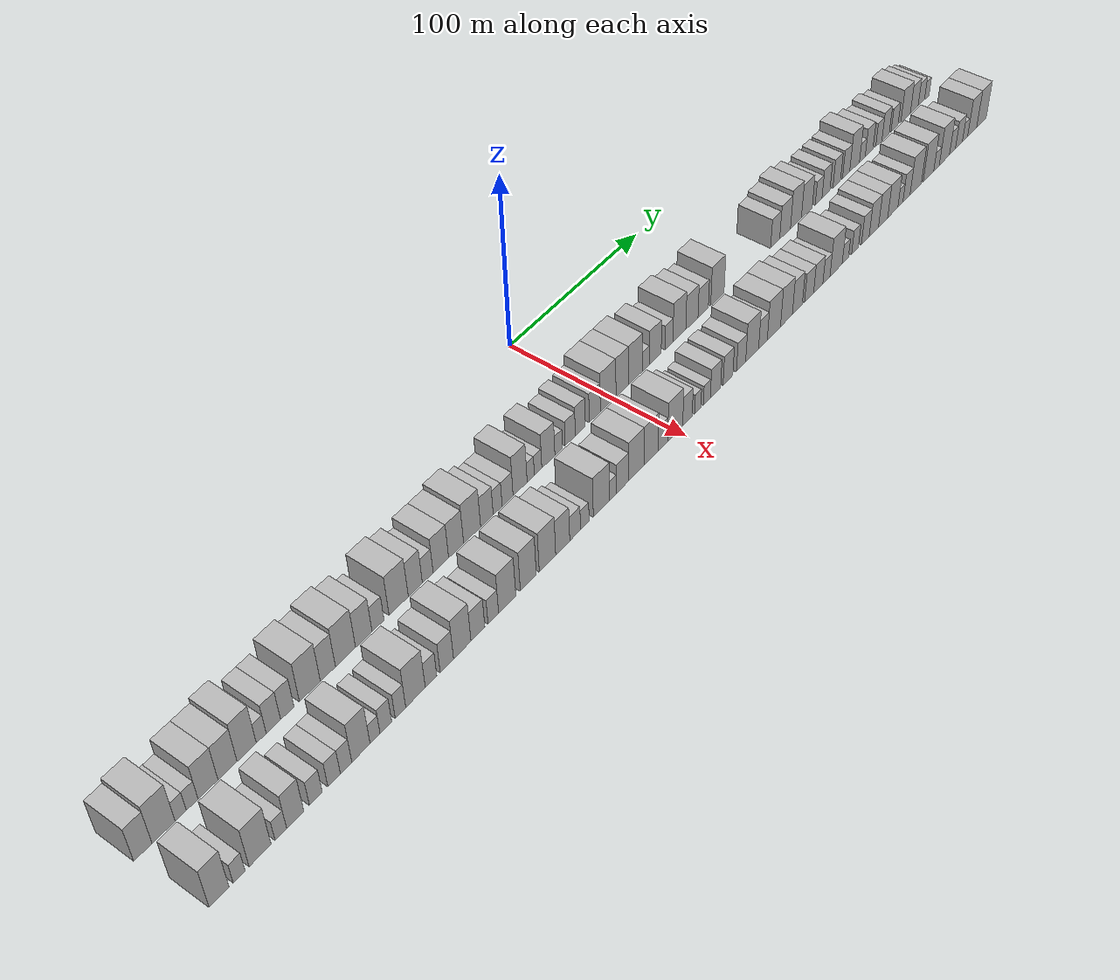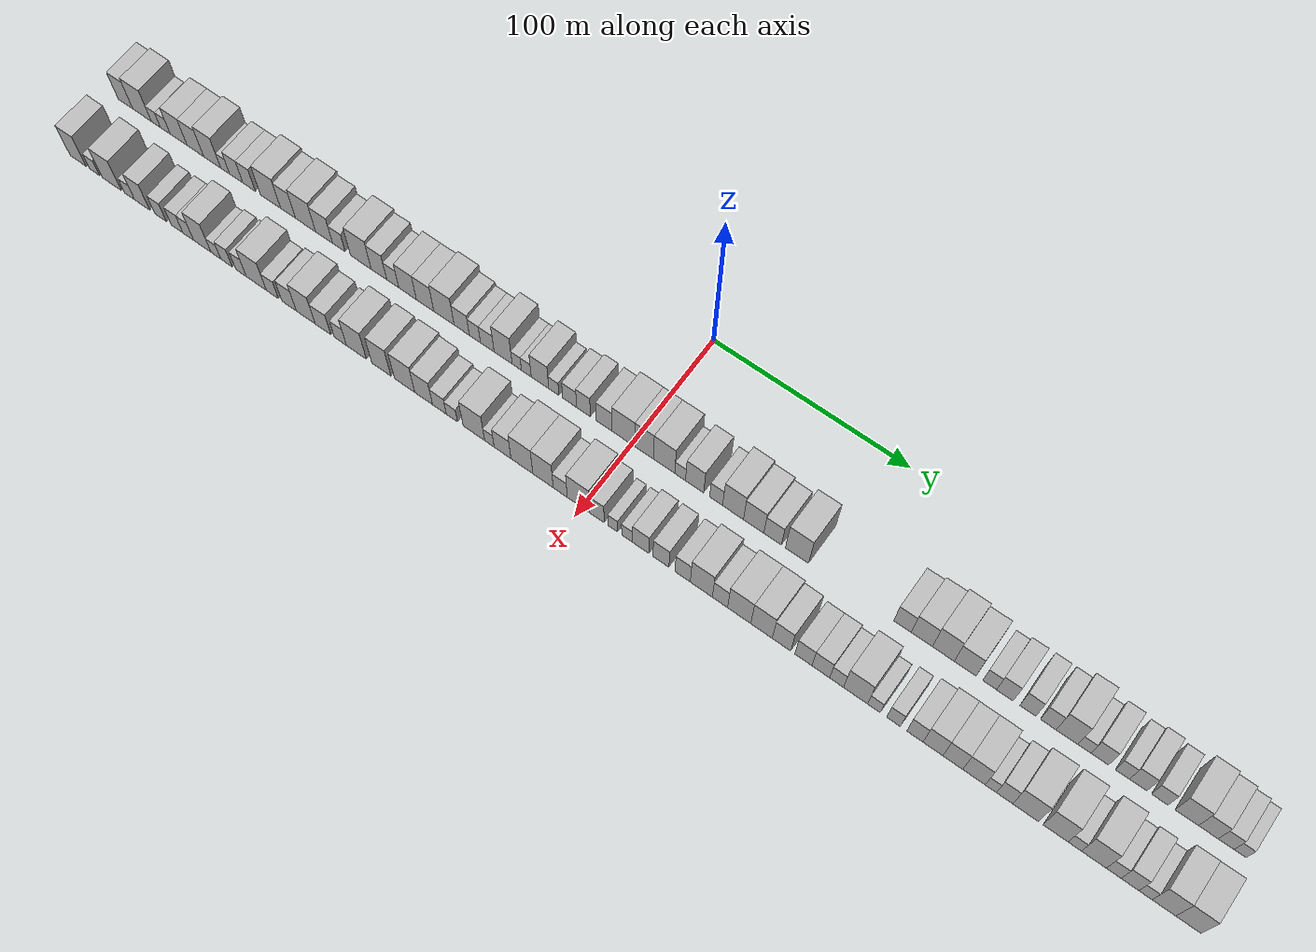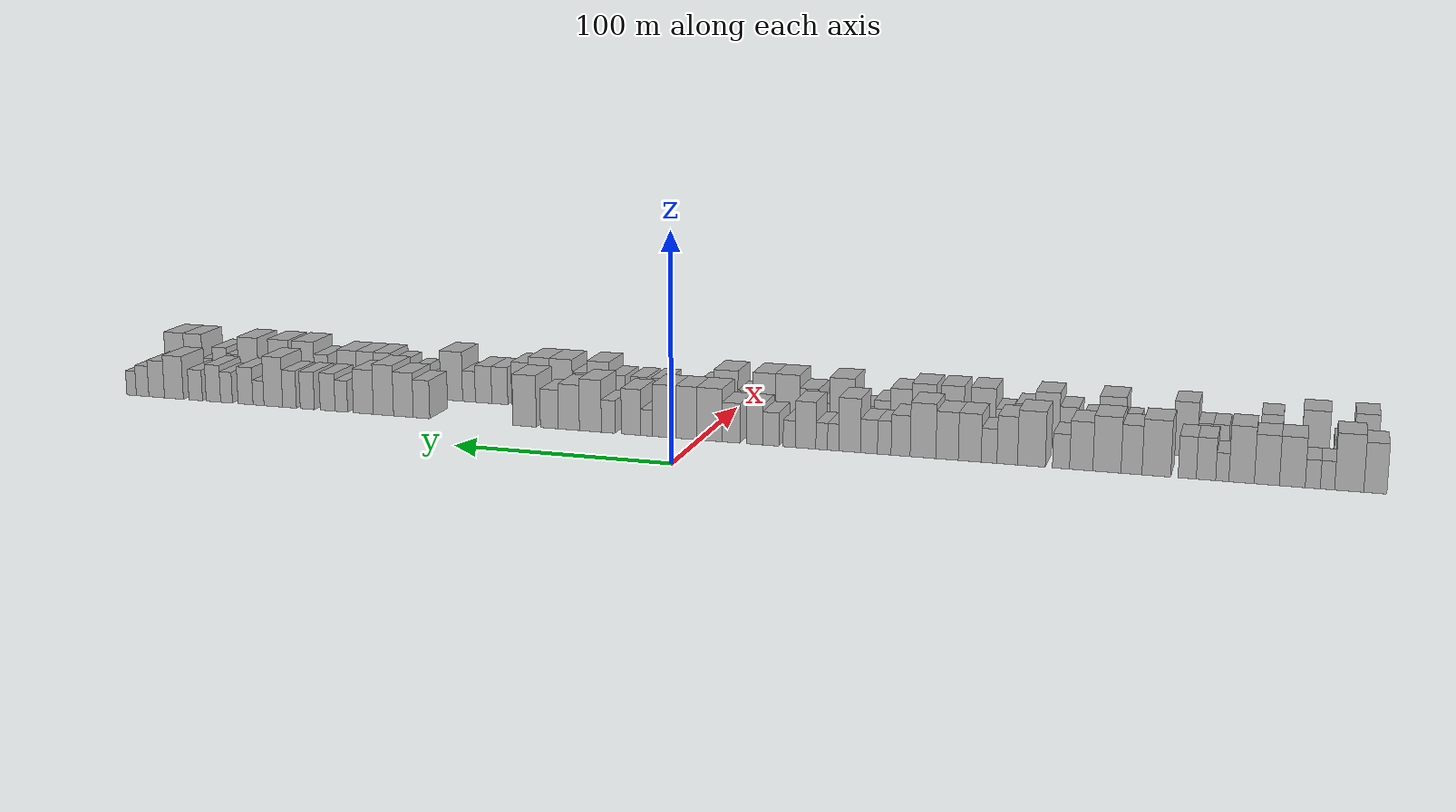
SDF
<sdf version="1.6">
 <world name="default">
  <scene>
   <sky><clouds><speed>12</speed></clouds></sky>
   <ambient>0.4 0.4 0.4 1</ambient>
   <background>0.7 0.7 0.7 1</background>
   <shadows>1</shadows>
  </scene>
  <gravity>0 0 -9.8066</gravity>
  <magnetic_field>6e-06 2.3e-05 -4.2e-05</magnetic_field>
  <physics default="0" name="default_physics" type="ode">
   <ode>
    <solver>
     <type>quick</type>
     <iters>10</iters>
     <sor>1.0</sor>
     <use_dynamic_moi_rescaling>0</use_dynamic_moi_rescaling>
    </solver>
    <constraints>
     <cfm>0</cfm>
     <erp>0.2</erp>
     <contact_max_correcting_vel>100</contact_max_correcting_vel>
     <contact_surface_layer>0.001</contact_surface_layer>
    </constraints>
   </ode>
   <max_step_size>0.004</max_step_size>
   <real_time_factor>1</real_time_factor>
   <real_time_update_rate>250</real_time_update_rate>
  </physics>
  <light name="sun" type="directional">
   <pose>0 0 10 0 0 0</pose>
   <diffuse>0.8 0.8 0.8 1</diffuse>
   <specular>0.2 0.2 0.2 1</specular>
   <attenuation>
    <range>1000</range>
    <constant>0.9</constant>
    <linear>0.01</linear>
    <quadratic>0.001</quadratic>
   </attenuation>
   <direction>-0.5 0.1 -0.9</direction>
  </light>
  <model name="building_1">
   <static>1</static>
   <pose>50.0000 -285.5545 0 0.000000 0.000000 0.000000</pose>
   <link name="link">
    <pose>0 0 10.50 0 0 0</pose>
    <collision name="collision"><geometry><box><size>20.0000 8.8911 21.0000</size></box></geometry></collision>
    <visual name="visual">
     <cast_shadows>0</cast_shadows>
     <geometry><box><size>20.0000 8.8911 21.0000</size></box></geometry>
     <material>
      <script>
       <uri>model://HANNAS_wall/materials/scripts</uri>
       <uri>model://HANNAS_wall/materials/textures</uri>
       <name>vrc/HANNAS_wall</name>
      </script>
     </material>
    </visual>
   </link>
  </model>
  <model name="building_2">
   <static>1</static>
   <pose>50.0000 -275.4508 0 0.000000 0.000000 0.000000</pose>
   <link name="link">
    <pose>0 0 12.00 0 0 0</pose>
    <collision name="collision"><geometry><box><size>20.0000 11.3163 24.0000</size></box></geometry></collision>
    <visual name="visual">
     <cast_shadows>0</cast_shadows>
     <geometry><box><size>20.0000 11.3163 24.0000</size></box></geometry>
     <material>
      <script>
       <uri>model://HANNAS_wall/materials/scripts</uri>
       <uri>model://HANNAS_wall/materials/textures</uri>
       <name>vrc/HANNAS_wall</name>
      </script>
     </material>
    </visual>
   </link>
  </model>
  <model name="building_3">
   <static>1</static>
   <pose>50.0000 -267.0089 0 0.000000 0.000000 0.000000</pose>
   <link name="link">
    <pose>0 0 6.00 0 0 0</pose>
    <collision name="collision"><geometry><box><size>20.0000 5.5675 12.0000</size></box></geometry></collision>
    <visual name="visual">
     <cast_shadows>0</cast_shadows>
     <geometry><box><size>20.0000 5.5675 12.0000</size></box></geometry>
     <material>
      <script>
       <uri>model://HANNAS_wall/materials/scripts</uri>
       <uri>model://HANNAS_wall/materials/textures</uri>
       <name>vrc/HANNAS_wall</name>
      </script>
     </material>
    </visual>
   </link>
  </model>
  <model name="building_4">
   <static>1</static>
   <pose>50.0000 -261.2701 0 0.000000 0.000000 0.000000</pose>
   <link name="link">
    <pose>0 0 6.00 0 0 0</pose>
    <collision name="collision"><geometry><box><size>20.0000 5.9101 12.0000</size></box></geometry></collision>
    <visual name="visual">
     <cast_shadows>0</cast_shadows>
     <geometry><box><size>20.0000 5.9101 12.0000</size></box></geometry>
     <material>
      <script>
       <uri>model://HANNAS_wall/materials/scripts</uri>
       <uri>model://HANNAS_wall/materials/textures</uri>
       <name>vrc/HANNAS_wall</name>
      </script>
     </material>
    </visual>
   </link>
  </model>
  <model name="building_5">
   <static>1</static>
   <pose>50.0000 -253.2307 0 0.000000 0.000000 0.000000</pose>
   <link name="link">
    <pose>0 0 10.50 0 0 0</pose>
    <collision name="collision"><geometry><box><size>20.0000 10.1686 21.0000</size></box></geometry></collision>
    <visual name="visual">
     <cast_shadows>0</cast_shadows>
     <geometry><box><size>20.0000 10.1686 21.0000</size></box></geometry>
     <material>
      <script>
       <uri>model://HANNAS_wall/materials/scripts</uri>
       <uri>model://HANNAS_wall/materials/textures</uri>
       <name>vrc/HANNAS_wall</name>
      </script>
     </material>
    </visual>
   </link>
  </model>
  <model name="building_6">
   <static>1</static>
   <pose>50.0000 -243.1957 0 0.000000 0.000000 0.000000</pose>
   <link name="link">
    <pose>0 0 10.50 0 0 0</pose>
    <collision name="collision"><geometry><box><size>20.0000 9.9014 21.0000</size></box></geometry></collision>
    <visual name="visual">
     <cast_shadows>0</cast_shadows>
     <geometry><box><size>20.0000 9.9014 21.0000</size></box></geometry>
     <material>
      <script>
       <uri>model://HANNAS_wall/materials/scripts</uri>
       <uri>model://HANNAS_wall/materials/textures</uri>
       <name>vrc/HANNAS_wall</name>
      </script>
     </material>
    </visual>
   </link>
  </model>
  <model name="building_7">
   <static>1</static>
   <pose>50.0000 -233.1583 0 0.000000 0.000000 0.000000</pose>
   <link name="link">
    <pose>0 0 12.00 0 0 0</pose>
    <collision name="collision"><geometry><box><size>20.0000 10.1734 24.0000</size></box></geometry></collision>
    <visual name="visual">
     <cast_shadows>0</cast_shadows>
     <geometry><box><size>20.0000 10.1734 24.0000</size></box></geometry>
     <material>
      <script>
       <uri>model://HANNAS_wall/materials/scripts</uri>
       <uri>model://HANNAS_wall/materials/textures</uri>
       <name>vrc/HANNAS_wall</name>
      </script>
     </material>
    </visual>
   </link>
  </model>
  <model name="building_8">
   <static>1</static>
   <pose>50.0000 -225.4317 0 0.000000 0.000000 0.000000</pose>
   <link name="link">
    <pose>0 0 6.00 0 0 0</pose>
    <collision name="collision"><geometry><box><size>20.0000 5.2798 12.0000</size></box></geometry></collision>
    <visual name="visual">
     <cast_shadows>0</cast_shadows>
     <geometry><box><size>20.0000 5.2798 12.0000</size></box></geometry>
     <material>
      <script>
       <uri>model://HANNAS_wall/materials/scripts</uri>
       <uri>model://HANNAS_wall/materials/textures</uri>
       <name>vrc/HANNAS_wall</name>
      </script>
     </material>
    </visual>
   </link>
  </model>
  <model name="building_9">
   <static>1</static>
   <pose>50.0000 -218.8903 0 0.000000 0.000000 0.000000</pose>
   <link name="link">
    <pose>0 0 9.00 0 0 0</pose>
    <collision name="collision"><geometry><box><size>20.0000 7.8029 18.0000</size></box></geometry></collision>
    <visual name="visual">
     <cast_shadows>0</cast_shadows>
     <geometry><box><size>20.0000 7.8029 18.0000</size></box></geometry>
     <material>
      <script>
       <uri>model://HANNAS_wall/materials/scripts</uri>
       <uri>model://HANNAS_wall/materials/textures</uri>
       <name>vrc/HANNAS_wall</name>
      </script>
     </material>
    </visual>
   </link>
  </model>
  <model name="building_10">
   <static>1</static>
   <pose>50.0000 -211.3066 0 0.000000 0.000000 0.000000</pose>
   <link name="link">
    <pose>0 0 9.00 0 0 0</pose>
    <collision name="collision"><geometry><box><size>20.0000 7.3646 18.0000</size></box></geometry></collision>
    <visual name="visual">
     <cast_shadows>0</cast_shadows>
     <geometry><box><size>20.0000 7.3646 18.0000</size></box></geometry>
     <material>
      <script>
       <uri>model://HANNAS_wall/materials/scripts</uri>
       <uri>model://HANNAS_wall/materials/textures</uri>
       <name>vrc/HANNAS_wall</name>
      </script>
     </material>
    </visual>
   </link>
  </model>
  <model name="building_11">
   <static>1</static>
   <pose>50.0000 -198.7508 0 0.000000 0.000000 0.000000</pose>
   <link name="link">
    <pose>0 0 12.00 0 0 0</pose>
    <collision name="collision"><geometry><box><size>20.0000 11.7470 24.0000</size></box></geometry></collision>
    <visual name="visual">
     <cast_shadows>0</cast_shadows>
     <geometry><box><size>20.0000 11.7470 24.0000</size></box></geometry>
     <material>
      <script>
       <uri>model://HANNAS_wall/materials/scripts</uri>
       <uri>model://HANNAS_wall/materials/textures</uri>
       <name>vrc/HANNAS_wall</name>
      </script>
     </material>
    </visual>
   </link>
  </model>
  <model name="building_12">
   <static>1</static>
   <pose>50.0000 -188.5699 0 0.000000 0.000000 0.000000</pose>
   <link name="link">
    <pose>0 0 10.50 0 0 0</pose>
    <collision name="collision"><geometry><box><size>20.0000 8.6148 21.0000</size></box></geometry></collision>
    <visual name="visual">
     <cast_shadows>0</cast_shadows>
     <geometry><box><size>20.0000 8.6148 21.0000</size></box></geometry>
     <material>
      <script>
       <uri>model://HANNAS_wall/materials/scripts</uri>
       <uri>model://HANNAS_wall/materials/textures</uri>
       <name>vrc/HANNAS_wall</name>
      </script>
     </material>
    </visual>
   </link>
  </model>
  <model name="building_13">
   <static>1</static>
   <pose>50.0000 -178.4441 0 0.000000 0.000000 0.000000</pose>
   <link name="link">
    <pose>0 0 12.00 0 0 0</pose>
    <collision name="collision"><geometry><box><size>20.0000 11.6368 24.0000</size></box></geometry></collision>
    <visual name="visual">
     <cast_shadows>0</cast_shadows>
     <geometry><box><size>20.0000 11.6368 24.0000</size></box></geometry>
     <material>
      <script>
       <uri>model://HANNAS_wall/materials/scripts</uri>
       <uri>model://HANNAS_wall/materials/textures</uri>
       <name>vrc/HANNAS_wall</name>
      </script>
     </material>
    </visual>
   </link>
  </model>
  <model name="building_14">
   <static>1</static>
   <pose>50.0000 -167.7657 0 0.000000 0.000000 0.000000</pose>
   <link name="link">
    <pose>0 0 10.50 0 0 0</pose>
    <collision name="collision"><geometry><box><size>20.0000 9.7201 21.0000</size></box></geometry></collision>
    <visual name="visual">
     <cast_shadows>0</cast_shadows>
     <geometry><box><size>20.0000 9.7201 21.0000</size></box></geometry>
     <material>
      <script>
       <uri>model://HANNAS_wall/materials/scripts</uri>
       <uri>model://HANNAS_wall/materials/textures</uri>
       <name>vrc/HANNAS_wall</name>
      </script>
     </material>
    </visual>
   </link>
  </model>
  <model name="building_15">
   <static>1</static>
   <pose>50.0000 -159.3174 0 0.000000 0.000000 0.000000</pose>
   <link name="link">
    <pose>0 0 7.50 0 0 0</pose>
    <collision name="collision"><geometry><box><size>20.0000 7.1764 15.0000</size></box></geometry></collision>
    <visual name="visual">
     <cast_shadows>0</cast_shadows>
     <geometry><box><size>20.0000 7.1764 15.0000</size></box></geometry>
     <material>
      <script>
       <uri>model://HANNAS_wall/materials/scripts</uri>
       <uri>model://HANNAS_wall/materials/textures</uri>
       <name>vrc/HANNAS_wall</name>
      </script>
     </material>
    </visual>
   </link>
  </model>
  <model name="building_16">
   <static>1</static>
   <pose>50.0000 -146.8509 0 0.000000 0.000000 0.000000</pose>
   <link name="link">
    <pose>0 0 12.00 0 0 0</pose>
    <collision name="collision"><geometry><box><size>20.0000 11.7566 24.0000</size></box></geometry></collision>
    <visual name="visual">
     <cast_shadows>0</cast_shadows>
     <geometry><box><size>20.0000 11.7566 24.0000</size></box></geometry>
     <material>
      <script>
       <uri>model://HANNAS_wall/materials/scripts</uri>
       <uri>model://HANNAS_wall/materials/textures</uri>
       <name>vrc/HANNAS_wall</name>
      </script>
     </material>
    </visual>
   </link>
  </model>
  <model name="building_17">
   <static>1</static>
   <pose>50.0000 -136.6007 0 0.000000 0.000000 0.000000</pose>
   <link name="link">
    <pose>0 0 10.50 0 0 0</pose>
    <collision name="collision"><geometry><box><size>20.0000 8.7438 21.0000</size></box></geometry></collision>
    <visual name="visual">
     <cast_shadows>0</cast_shadows>
     <geometry><box><size>20.0000 8.7438 21.0000</size></box></geometry>
     <material>
      <script>
       <uri>model://HANNAS_wall/materials/scripts</uri>
       <uri>model://HANNAS_wall/materials/textures</uri>
       <name>vrc/HANNAS_wall</name>
      </script>
     </material>
    </visual>
   </link>
  </model>
  <model name="building_18">
   <static>1</static>
   <pose>50.0000 -128.8635 0 0.000000 0.000000 0.000000</pose>
   <link name="link">
    <pose>0 0 7.50 0 0 0</pose>
    <collision name="collision"><geometry><box><size>20.0000 6.7308 15.0000</size></box></geometry></collision>
    <visual name="visual">
     <cast_shadows>0</cast_shadows>
     <geometry><box><size>20.0000 6.7308 15.0000</size></box></geometry>
     <material>
      <script>
       <uri>model://HANNAS_wall/materials/scripts</uri>
       <uri>model://HANNAS_wall/materials/textures</uri>
       <name>vrc/HANNAS_wall</name>
      </script>
     </material>
    </visual>
   </link>
  </model>
  <model name="building_19">
   <static>1</static>
   <pose>50.0000 -120.5768 0 0.000000 0.000000 0.000000</pose>
   <link name="link">
    <pose>0 0 10.50 0 0 0</pose>
    <collision name="collision"><geometry><box><size>20.0000 9.8427 21.0000</size></box></geometry></collision>
    <visual name="visual">
     <cast_shadows>0</cast_shadows>
     <geometry><box><size>20.0000 9.8427 21.0000</size></box></geometry>
     <material>
      <script>
       <uri>model://HANNAS_wall/materials/scripts</uri>
       <uri>model://HANNAS_wall/materials/textures</uri>
       <name>vrc/HANNAS_wall</name>
      </script>
     </material>
    </visual>
   </link>
  </model>
  <model name="building_20">
   <static>1</static>
   <pose>50.0000 -110.8102 0 0.000000 0.000000 0.000000</pose>
   <link name="link">
    <pose>0 0 10.50 0 0 0</pose>
    <collision name="collision"><geometry><box><size>20.0000 9.6905 21.0000</size></box></geometry></collision>
    <visual name="visual">
     <cast_shadows>0</cast_shadows>
     <geometry><box><size>20.0000 9.6905 21.0000</size></box></geometry>
     <material>
      <script>
       <uri>model://HANNAS_wall/materials/scripts</uri>
       <uri>model://HANNAS_wall/materials/textures</uri>
       <name>vrc/HANNAS_wall</name>
      </script>
     </material>
    </visual>
   </link>
  </model>
  <model name="building_21">
   <static>1</static>
   <pose>50.0000 -100.3670 0 0.000000 0.000000 0.000000</pose>
   <link name="link">
    <pose>0 0 12.00 0 0 0</pose>
    <collision name="collision"><geometry><box><size>20.0000 11.1959 24.0000</size></box></geometry></collision>
    <visual name="visual">
     <cast_shadows>0</cast_shadows>
     <geometry><box><size>20.0000 11.1959 24.0000</size></box></geometry>
     <material>
      <script>
       <uri>model://HANNAS_wall/materials/scripts</uri>
       <uri>model://HANNAS_wall/materials/textures</uri>
       <name>vrc/HANNAS_wall</name>
      </script>
     </material>
    </visual>
   </link>
  </model>
  <model name="building_22">
   <static>1</static>
   <pose>50.0000 -90.5872 0 0.000000 0.000000 0.000000</pose>
   <link name="link">
    <pose>0 0 9.00 0 0 0</pose>
    <collision name="collision"><geometry><box><size>20.0000 8.3636 18.0000</size></box></geometry></collision>
    <visual name="visual">
     <cast_shadows>0</cast_shadows>
     <geometry><box><size>20.0000 8.3636 18.0000</size></box></geometry>
     <material>
      <script>
       <uri>model://HANNAS_wall/materials/scripts</uri>
       <uri>model://HANNAS_wall/materials/textures</uri>
       <name>vrc/HANNAS_wall</name>
      </script>
     </material>
    </visual>
   </link>
  </model>
  <model name="building_23">
   <static>1</static>
   <pose>50.0000 -83.3970 0 0.000000 0.000000 0.000000</pose>
   <link name="link">
    <pose>0 0 7.50 0 0 0</pose>
    <collision name="collision"><geometry><box><size>20.0000 6.0168 15.0000</size></box></geometry></collision>
    <visual name="visual">
     <cast_shadows>0</cast_shadows>
     <geometry><box><size>20.0000 6.0168 15.0000</size></box></geometry>
     <material>
      <script>
       <uri>model://HANNAS_wall/materials/scripts</uri>
       <uri>model://HANNAS_wall/materials/textures</uri>
       <name>vrc/HANNAS_wall</name>
      </script>
     </material>
    </visual>
   </link>
  </model>
  <model name="building_24">
   <static>1</static>
   <pose>50.0000 -76.6673 0 0.000000 0.000000 0.000000</pose>
   <link name="link">
    <pose>0 0 7.50 0 0 0</pose>
    <collision name="collision"><geometry><box><size>20.0000 7.4427 15.0000</size></box></geometry></collision>
    <visual name="visual">
     <cast_shadows>0</cast_shadows>
     <geometry><box><size>20.0000 7.4427 15.0000</size></box></geometry>
     <material>
      <script>
       <uri>model://HANNAS_wall/materials/scripts</uri>
       <uri>model://HANNAS_wall/materials/textures</uri>
       <name>vrc/HANNAS_wall</name>
      </script>
     </material>
    </visual>
   </link>
  </model>
  <model name="building_25">
   <static>1</static>
   <pose>50.0000 -68.0999 0 0.000000 0.000000 0.000000</pose>
   <link name="link">
    <pose>0 0 12.00 0 0 0</pose>
    <collision name="collision"><geometry><box><size>20.0000 9.6921 24.0000</size></box></geometry></collision>
    <visual name="visual">
     <cast_shadows>0</cast_shadows>
     <geometry><box><size>20.0000 9.6921 24.0000</size></box></geometry>
     <material>
      <script>
       <uri>model://HANNAS_wall/materials/scripts</uri>
       <uri>model://HANNAS_wall/materials/textures</uri>
       <name>vrc/HANNAS_wall</name>
      </script>
     </material>
    </visual>
   </link>
  </model>
  <model name="building_26">
   <static>1</static>
   <pose>50.0000 -60.7385 0 0.000000 0.000000 0.000000</pose>
   <link name="link">
    <pose>0 0 6.00 0 0 0</pose>
    <collision name="collision"><geometry><box><size>20.0000 5.0307 12.0000</size></box></geometry></collision>
    <visual name="visual">
     <cast_shadows>0</cast_shadows>
     <geometry><box><size>20.0000 5.0307 12.0000</size></box></geometry>
     <material>
      <script>
       <uri>model://HANNAS_wall/materials/scripts</uri>
       <uri>model://HANNAS_wall/materials/textures</uri>
       <name>vrc/HANNAS_wall</name>
      </script>
     </material>
    </visual>
   </link>
  </model>
  <model name="building_27">
   <static>1</static>
   <pose>50.0000 -55.6057 0 0.000000 0.000000 0.000000</pose>
   <link name="link">
    <pose>0 0 6.00 0 0 0</pose>
    <collision name="collision"><geometry><box><size>20.0000 5.2350 12.0000</size></box></geometry></collision>
    <visual name="visual">
     <cast_shadows>0</cast_shadows>
     <geometry><box><size>20.0000 5.2350 12.0000</size></box></geometry>
     <material>
      <script>
       <uri>model://HANNAS_wall/materials/scripts</uri>
       <uri>model://HANNAS_wall/materials/textures</uri>
       <name>vrc/HANNAS_wall</name>
      </script>
     </material>
    </visual>
   </link>
  </model>
  <model name="building_28">
   <static>1</static>
   <pose>50.0000 -48.3343 0 0.000000 0.000000 0.000000</pose>
   <link name="link">
    <pose>0 0 10.50 0 0 0</pose>
    <collision name="collision"><geometry><box><size>20.0000 9.3079 21.0000</size></box></geometry></collision>
    <visual name="visual">
     <cast_shadows>0</cast_shadows>
     <geometry><box><size>20.0000 9.3079 21.0000</size></box></geometry>
     <material>
      <script>
       <uri>model://HANNAS_wall/materials/scripts</uri>
       <uri>model://HANNAS_wall/materials/textures</uri>
       <name>vrc/HANNAS_wall</name>
      </script>
     </material>
    </visual>
   </link>
  </model>
  <model name="building_29">
   <static>1</static>
   <pose>50.0000 -40.9712 0 0.000000 0.000000 0.000000</pose>
   <link name="link">
    <pose>0 0 6.00 0 0 0</pose>
    <collision name="collision"><geometry><box><size>20.0000 5.4182 12.0000</size></box></geometry></collision>
    <visual name="visual">
     <cast_shadows>0</cast_shadows>
     <geometry><box><size>20.0000 5.4182 12.0000</size></box></geometry>
     <material>
      <script>
       <uri>model://HANNAS_wall/materials/scripts</uri>
       <uri>model://HANNAS_wall/materials/textures</uri>
       <name>vrc/HANNAS_wall</name>
      </script>
     </material>
    </visual>
   </link>
  </model>
  <model name="building_30">
   <static>1</static>
   <pose>50.0000 -32.5874 0 0.000000 0.000000 0.000000</pose>
   <link name="link">
    <pose>0 0 7.50 0 0 0</pose>
    <collision name="collision"><geometry><box><size>20.0000 7.3494 15.0000</size></box></geometry></collision>
    <visual name="visual">
     <cast_shadows>0</cast_shadows>
     <geometry><box><size>20.0000 7.3494 15.0000</size></box></geometry>
     <material>
      <script>
       <uri>model://HANNAS_wall/materials/scripts</uri>
       <uri>model://HANNAS_wall/materials/textures</uri>
       <name>vrc/HANNAS_wall</name>
      </script>
     </material>
    </visual>
   </link>
  </model>
  <model name="building_31">
   <static>1</static>
   <pose>50.0000 -25.2734 0 0.000000 0.000000 0.000000</pose>
   <link name="link">
    <pose>0 0 9.00 0 0 0</pose>
    <collision name="collision"><geometry><box><size>20.0000 7.2786 18.0000</size></box></geometry></collision>
    <visual name="visual">
     <cast_shadows>0</cast_shadows>
     <geometry><box><size>20.0000 7.2786 18.0000</size></box></geometry>
     <material>
      <script>
       <uri>model://HANNAS_wall/materials/scripts</uri>
       <uri>model://HANNAS_wall/materials/textures</uri>
       <name>vrc/HANNAS_wall</name>
      </script>
     </material>
    </visual>
   </link>
  </model>
  <model name="building_32">
   <static>1</static>
   <pose>50.0000 -14.4998 0 0.000000 0.000000 0.000000</pose>
   <link name="link">
    <pose>0 0 9.00 0 0 0</pose>
    <collision name="collision"><geometry><box><size>20.0000 8.2685 18.0000</size></box></geometry></collision>
    <visual name="visual">
     <cast_shadows>0</cast_shadows>
     <geometry><box><size>20.0000 8.2685 18.0000</size></box></geometry>
     <material>
      <script>
       <uri>model://HANNAS_wall/materials/scripts</uri>
       <uri>model://HANNAS_wall/materials/textures</uri>
       <name>vrc/HANNAS_wall</name>
      </script>
     </material>
    </visual>
   </link>
  </model>
  <model name="building_33">
   <static>1</static>
   <pose>50.0000 -4.4543 0 0.000000 0.000000 0.000000</pose>
   <link name="link">
    <pose>0 0 12.00 0 0 0</pose>
    <collision name="collision"><geometry><box><size>20.0000 11.8226 24.0000</size></box></geometry></collision>
    <visual name="visual">
     <cast_shadows>0</cast_shadows>
     <geometry><box><size>20.0000 11.8226 24.0000</size></box></geometry>
     <material>
      <script>
       <uri>model://HANNAS_wall/materials/scripts</uri>
       <uri>model://HANNAS_wall/materials/textures</uri>
       <name>vrc/HANNAS_wall</name>
      </script>
     </material>
    </visual>
   </link>
  </model>
  <model name="building_34">
   <static>1</static>
   <pose>50.0000 6.3101 0 0.000000 0.000000 0.000000</pose>
   <link name="link">
    <pose>0 0 12.00 0 0 0</pose>
    <collision name="collision"><geometry><box><size>20.0000 9.7060 24.0000</size></box></geometry></collision>
    <visual name="visual">
     <cast_shadows>0</cast_shadows>
     <geometry><box><size>20.0000 9.7060 24.0000</size></box></geometry>
     <material>
      <script>
       <uri>model://HANNAS_wall/materials/scripts</uri>
       <uri>model://HANNAS_wall/materials/textures</uri>
       <name>vrc/HANNAS_wall</name>
      </script>
     </material>
    </visual>
   </link>
  </model>
  <model name="building_35">
   <static>1</static>
   <pose>50.0000 16.6346 0 0.000000 0.000000 0.000000</pose>
   <link name="link">
    <pose>0 0 12.00 0 0 0</pose>
    <collision name="collision"><geometry><box><size>20.0000 10.9430 24.0000</size></box></geometry></collision>
    <visual name="visual">
     <cast_shadows>0</cast_shadows>
     <geometry><box><size>20.0000 10.9430 24.0000</size></box></geometry>
     <material>
      <script>
       <uri>model://HANNAS_wall/materials/scripts</uri>
       <uri>model://HANNAS_wall/materials/textures</uri>
       <name>vrc/HANNAS_wall</name>
      </script>
     </material>
    </visual>
   </link>
  </model>
  <model name="building_36">
   <static>1</static>
   <pose>50.0000 24.8381 0 0.000000 0.000000 0.000000</pose>
   <link name="link">
    <pose>0 0 6.00 0 0 0</pose>
    <collision name="collision"><geometry><box><size>20.0000 5.4641 12.0000</size></box></geometry></collision>
    <visual name="visual">
     <cast_shadows>0</cast_shadows>
     <geometry><box><size>20.0000 5.4641 12.0000</size></box></geometry>
     <material>
      <script>
       <uri>model://HANNAS_wall/materials/scripts</uri>
       <uri>model://HANNAS_wall/materials/textures</uri>
       <name>vrc/HANNAS_wall</name>
      </script>
     </material>
    </visual>
   </link>
  </model>
  <model name="building_37">
   <static>1</static>
   <pose>50.0000 32.2049 0 0.000000 0.000000 0.000000</pose>
   <link name="link">
    <pose>0 0 10.50 0 0 0</pose>
    <collision name="collision"><geometry><box><size>20.0000 9.2696 21.0000</size></box></geometry></collision>
    <visual name="visual">
     <cast_shadows>0</cast_shadows>
     <geometry><box><size>20.0000 9.2696 21.0000</size></box></geometry>
     <material>
      <script>
       <uri>model://HANNAS_wall/materials/scripts</uri>
       <uri>model://HANNAS_wall/materials/textures</uri>
       <name>vrc/HANNAS_wall</name>
      </script>
     </material>
    </visual>
   </link>
  </model>
  <model name="building_38">
   <static>1</static>
   <pose>50.0000 43.1029 0 0.000000 0.000000 0.000000</pose>
   <link name="link">
    <pose>0 0 7.50 0 0 0</pose>
    <collision name="collision"><geometry><box><size>20.0000 6.5264 15.0000</size></box></geometry></collision>
    <visual name="visual">
     <cast_shadows>0</cast_shadows>
     <geometry><box><size>20.0000 6.5264 15.0000</size></box></geometry>
     <material>
      <script>
       <uri>model://HANNAS_wall/materials/scripts</uri>
       <uri>model://HANNAS_wall/materials/textures</uri>
       <name>vrc/HANNAS_wall</name>
      </script>
     </material>
    </visual>
   </link>
  </model>
  <model name="building_39">
   <static>1</static>
   <pose>50.0000 51.6203 0 0.000000 0.000000 0.000000</pose>
   <link name="link">
    <pose>0 0 12.00 0 0 0</pose>
    <collision name="collision"><geometry><box><size>20.0000 10.5083 24.0000</size></box></geometry></collision>
    <visual name="visual">
     <cast_shadows>0</cast_shadows>
     <geometry><box><size>20.0000 10.5083 24.0000</size></box></geometry>
     <material>
      <script>
       <uri>model://HANNAS_wall/materials/scripts</uri>
       <uri>model://HANNAS_wall/materials/textures</uri>
       <name>vrc/HANNAS_wall</name>
      </script>
     </material>
    </visual>
   </link>
  </model>
  <model name="building_40">
   <static>1</static>
   <pose>50.0000 61.9553 0 0.000000 0.000000 0.000000</pose>
   <link name="link">
    <pose>0 0 10.50 0 0 0</pose>
    <collision name="collision"><geometry><box><size>20.0000 10.1617 21.0000</size></box></geometry></collision>
    <visual name="visual">
     <cast_shadows>0</cast_shadows>
     <geometry><box><size>20.0000 10.1617 21.0000</size></box></geometry>
     <material>
      <script>
       <uri>model://HANNAS_wall/materials/scripts</uri>
       <uri>model://HANNAS_wall/materials/textures</uri>
       <name>vrc/HANNAS_wall</name>
      </script>
     </material>
    </visual>
   </link>
  </model>
  <model name="building_41">
   <static>1</static>
   <pose>50.0000 71.3873 0 0.000000 0.000000 0.000000</pose>
   <link name="link">
    <pose>0 0 9.00 0 0 0</pose>
    <collision name="collision"><geometry><box><size>20.0000 8.7023 18.0000</size></box></geometry></collision>
    <visual name="visual">
     <cast_shadows>0</cast_shadows>
     <geometry><box><size>20.0000 8.7023 18.0000</size></box></geometry>
     <material>
      <script>
       <uri>model://HANNAS_wall/materials/scripts</uri>
       <uri>model://HANNAS_wall/materials/textures</uri>
       <name>vrc/HANNAS_wall</name>
      </script>
     </material>
    </visual>
   </link>
  </model>
  <model name="building_42">
   <static>1</static>
   <pose>50.0000 83.4444 0 0.000000 0.000000 0.000000</pose>
   <link name="link">
    <pose>0 0 12.00 0 0 0</pose>
    <collision name="collision"><geometry><box><size>20.0000 11.4119 24.0000</size></box></geometry></collision>
    <visual name="visual">
     <cast_shadows>0</cast_shadows>
     <geometry><box><size>20.0000 11.4119 24.0000</size></box></geometry>
     <material>
      <script>
       <uri>model://HANNAS_wall/materials/scripts</uri>
       <uri>model://HANNAS_wall/materials/textures</uri>
       <name>vrc/HANNAS_wall</name>
      </script>
     </material>
    </visual>
   </link>
  </model>
  <model name="building_43">
   <static>1</static>
   <pose>50.0000 134.6343 0 0.000000 0.000000 0.000000</pose>
   <link name="link">
    <pose>0 0 9.00 0 0 0</pose>
    <collision name="collision"><geometry><box><size>20.0000 8.3227 18.0000</size></box></geometry></collision>
    <visual name="visual">
     <cast_shadows>0</cast_shadows>
     <geometry><box><size>20.0000 8.3227 18.0000</size></box></geometry>
     <material>
      <script>
       <uri>model://HANNAS_wall/materials/scripts</uri>
       <uri>model://HANNAS_wall/materials/textures</uri>
       <name>vrc/HANNAS_wall</name>
      </script>
     </material>
    </visual>
   </link>
  </model>
  <model name="building_44">
   <static>1</static>
   <pose>50.0000 143.7940 0 0.000000 0.000000 0.000000</pose>
   <link name="link">
    <pose>0 0 10.50 0 0 0</pose>
    <collision name="collision"><geometry><box><size>20.0000 9.9968 21.0000</size></box></geometry></collision>
    <visual name="visual">
     <cast_shadows>0</cast_shadows>
     <geometry><box><size>20.0000 9.9968 21.0000</size></box></geometry>
     <material>
      <script>
       <uri>model://HANNAS_wall/materials/scripts</uri>
       <uri>model://HANNAS_wall/materials/textures</uri>
       <name>vrc/HANNAS_wall</name>
      </script>
     </material>
    </visual>
   </link>
  </model>
  <model name="building_45">
   <static>1</static>
   <pose>50.0000 153.9346 0 0.000000 0.000000 0.000000</pose>
   <link name="link">
    <pose>0 0 12.00 0 0 0</pose>
    <collision name="collision"><geometry><box><size>20.0000 10.2844 24.0000</size></box></geometry></collision>
    <visual name="visual">
     <cast_shadows>0</cast_shadows>
     <geometry><box><size>20.0000 10.2844 24.0000</size></box></geometry>
     <material>
      <script>
       <uri>model://HANNAS_wall/materials/scripts</uri>
       <uri>model://HANNAS_wall/materials/textures</uri>
       <name>vrc/HANNAS_wall</name>
      </script>
     </material>
    </visual>
   </link>
  </model>
  <model name="building_46">
   <static>1</static>
   <pose>50.0000 164.1987 0 0.000000 0.000000 0.000000</pose>
   <link name="link">
    <pose>0 0 10.50 0 0 0</pose>
    <collision name="collision"><geometry><box><size>20.0000 10.2437 21.0000</size></box></geometry></collision>
    <visual name="visual">
     <cast_shadows>0</cast_shadows>
     <geometry><box><size>20.0000 10.2437 21.0000</size></box></geometry>
     <material>
      <script>
       <uri>model://HANNAS_wall/materials/scripts</uri>
       <uri>model://HANNAS_wall/materials/textures</uri>
       <name>vrc/HANNAS_wall</name>
      </script>
     </material>
    </visual>
   </link>
  </model>
  <model name="building_47">
   <static>1</static>
   <pose>50.0000 175.5578 0 0.000000 0.000000 0.000000</pose>
   <link name="link">
    <pose>0 0 7.50 0 0 0</pose>
    <collision name="collision"><geometry><box><size>20.0000 6.4744 15.0000</size></box></geometry></collision>
    <visual name="visual">
     <cast_shadows>0</cast_shadows>
     <geometry><box><size>20.0000 6.4744 15.0000</size></box></geometry>
     <material>
      <script>
       <uri>model://HANNAS_wall/materials/scripts</uri>
       <uri>model://HANNAS_wall/materials/textures</uri>
       <name>vrc/HANNAS_wall</name>
      </script>
     </material>
    </visual>
   </link>
  </model>
  <model name="building_48">
   <static>1</static>
   <pose>50.0000 182.6504 0 0.000000 0.000000 0.000000</pose>
   <link name="link">
    <pose>0 0 9.00 0 0 0</pose>
    <collision name="collision"><geometry><box><size>20.0000 7.7110 18.0000</size></box></geometry></collision>
    <visual name="visual">
     <cast_shadows>0</cast_shadows>
     <geometry><box><size>20.0000 7.7110 18.0000</size></box></geometry>
     <material>
      <script>
       <uri>model://HANNAS_wall/materials/scripts</uri>
       <uri>model://HANNAS_wall/materials/textures</uri>
       <name>vrc/HANNAS_wall</name>
      </script>
     </material>
    </visual>
   </link>
  </model>
  <model name="building_49">
   <static>1</static>
   <pose>50.0000 193.2254 0 0.000000 0.000000 0.000000</pose>
   <link name="link">
    <pose>0 0 9.00 0 0 0</pose>
    <collision name="collision"><geometry><box><size>20.0000 7.4389 18.0000</size></box></geometry></collision>
    <visual name="visual">
     <cast_shadows>0</cast_shadows>
     <geometry><box><size>20.0000 7.4389 18.0000</size></box></geometry>
     <material>
      <script>
       <uri>model://HANNAS_wall/materials/scripts</uri>
       <uri>model://HANNAS_wall/materials/textures</uri>
       <name>vrc/HANNAS_wall</name>
      </script>
     </material>
    </visual>
   </link>
  </model>
  <model name="building_50">
   <static>1</static>
   <pose>50.0000 202.5473 0 0.000000 0.000000 0.000000</pose>
   <link name="link">
    <pose>0 0 9.00 0 0 0</pose>
    <collision name="collision"><geometry><box><size>20.0000 7.2050 18.0000</size></box></geometry></collision>
    <visual name="visual">
     <cast_shadows>0</cast_shadows>
     <geometry><box><size>20.0000 7.2050 18.0000</size></box></geometry>
     <material>
      <script>
       <uri>model://HANNAS_wall/materials/scripts</uri>
       <uri>model://HANNAS_wall/materials/textures</uri>
       <name>vrc/HANNAS_wall</name>
      </script>
     </material>
    </visual>
   </link>
  </model>
  <model name="building_51">
   <static>1</static>
   <pose>50.0000 211.0968 0 0.000000 0.000000 0.000000</pose>
   <link name="link">
    <pose>0 0 12.00 0 0 0</pose>
    <collision name="collision"><geometry><box><size>20.0000 9.8938 24.0000</size></box></geometry></collision>
    <visual name="visual">
     <cast_shadows>0</cast_shadows>
     <geometry><box><size>20.0000 9.8938 24.0000</size></box></geometry>
     <material>
      <script>
       <uri>model://HANNAS_wall/materials/scripts</uri>
       <uri>model://HANNAS_wall/materials/textures</uri>
       <name>vrc/HANNAS_wall</name>
      </script>
     </material>
    </visual>
   </link>
  </model>
  <model name="building_52">
   <static>1</static>
   <pose>50.0000 218.9433 0 0.000000 0.000000 0.000000</pose>
   <link name="link">
    <pose>0 0 6.00 0 0 0</pose>
    <collision name="collision"><geometry><box><size>20.0000 5.7993 12.0000</size></box></geometry></collision>
    <visual name="visual">
     <cast_shadows>0</cast_shadows>
     <geometry><box><size>20.0000 5.7993 12.0000</size></box></geometry>
     <material>
      <script>
       <uri>model://HANNAS_wall/materials/scripts</uri>
       <uri>model://HANNAS_wall/materials/textures</uri>
       <name>vrc/HANNAS_wall</name>
      </script>
     </material>
    </visual>
   </link>
  </model>
  <model name="building_53">
   <static>1</static>
   <pose>50.0000 225.8257 0 0.000000 0.000000 0.000000</pose>
   <link name="link">
    <pose>0 0 9.00 0 0 0</pose>
    <collision name="collision"><geometry><box><size>20.0000 7.9656 18.0000</size></box></geometry></collision>
    <visual name="visual">
     <cast_shadows>0</cast_shadows>
     <geometry><box><size>20.0000 7.9656 18.0000</size></box></geometry>
     <material>
      <script>
       <uri>model://HANNAS_wall/materials/scripts</uri>
       <uri>model://HANNAS_wall/materials/textures</uri>
       <name>vrc/HANNAS_wall</name>
      </script>
     </material>
    </visual>
   </link>
  </model>
  <model name="building_54">
   <static>1</static>
   <pose>50.0000 235.9830 0 0.000000 0.000000 0.000000</pose>
   <link name="link">
    <pose>0 0 7.50 0 0 0</pose>
    <collision name="collision"><geometry><box><size>20.0000 6.3490 15.0000</size></box></geometry></collision>
    <visual name="visual">
     <cast_shadows>0</cast_shadows>
     <geometry><box><size>20.0000 6.3490 15.0000</size></box></geometry>
     <material>
      <script>
       <uri>model://HANNAS_wall/materials/scripts</uri>
       <uri>model://HANNAS_wall/materials/textures</uri>
       <name>vrc/HANNAS_wall</name>
      </script>
     </material>
    </visual>
   </link>
  </model>
  <model name="building_55">
   <static>1</static>
   <pose>50.0000 243.0241 0 0.000000 0.000000 0.000000</pose>
   <link name="link">
    <pose>0 0 9.00 0 0 0</pose>
    <collision name="collision"><geometry><box><size>20.0000 7.7330 18.0000</size></box></geometry></collision>
    <visual name="visual">
     <cast_shadows>0</cast_shadows>
     <geometry><box><size>20.0000 7.7330 18.0000</size></box></geometry>
     <material>
      <script>
       <uri>model://HANNAS_wall/materials/scripts</uri>
       <uri>model://HANNAS_wall/materials/textures</uri>
       <name>vrc/HANNAS_wall</name>
      </script>
     </material>
    </visual>
   </link>
  </model>
  <model name="building_56">
   <static>1</static>
   <pose>50.0000 252.5628 0 0.000000 0.000000 0.000000</pose>
   <link name="link">
    <pose>0 0 7.50 0 0 0</pose>
    <collision name="collision"><geometry><box><size>20.0000 7.3444 15.0000</size></box></geometry></collision>
    <visual name="visual">
     <cast_shadows>0</cast_shadows>
     <geometry><box><size>20.0000 7.3444 15.0000</size></box></geometry>
     <material>
      <script>
       <uri>model://HANNAS_wall/materials/scripts</uri>
       <uri>model://HANNAS_wall/materials/textures</uri>
       <name>vrc/HANNAS_wall</name>
      </script>
     </material>
    </visual>
   </link>
  </model>
  <model name="building_57">
   <static>1</static>
   <pose>50.0000 264.3889 0 0.000000 0.000000 0.000000</pose>
   <link name="link">
    <pose>0 0 10.50 0 0 0</pose>
    <collision name="collision"><geometry><box><size>20.0000 10.3080 21.0000</size></box></geometry></collision>
    <visual name="visual">
     <cast_shadows>0</cast_shadows>
     <geometry><box><size>20.0000 10.3080 21.0000</size></box></geometry>
     <material>
      <script>
       <uri>model://HANNAS_wall/materials/scripts</uri>
       <uri>model://HANNAS_wall/materials/textures</uri>
       <name>vrc/HANNAS_wall</name>
      </script>
     </material>
    </visual>
   </link>
  </model>
  <model name="building_58">
   <static>1</static>
   <pose>50.0000 273.8150 0 0.000000 0.000000 0.000000</pose>
   <link name="link">
    <pose>0 0 9.00 0 0 0</pose>
    <collision name="collision"><geometry><box><size>20.0000 8.5441 18.0000</size></box></geometry></collision>
    <visual name="visual">
     <cast_shadows>0</cast_shadows>
     <geometry><box><size>20.0000 8.5441 18.0000</size></box></geometry>
     <material>
      <script>
       <uri>model://HANNAS_wall/materials/scripts</uri>
       <uri>model://HANNAS_wall/materials/textures</uri>
       <name>vrc/HANNAS_wall</name>
      </script>
     </material>
    </visual>
   </link>
  </model>
  <model name="building_59">
   <static>1</static>
   <pose>50.0000 281.5288 0 0.000000 0.000000 0.000000</pose>
   <link name="link">
    <pose>0 0 7.50 0 0 0</pose>
    <collision name="collision"><geometry><box><size>20.0000 6.8836 15.0000</size></box></geometry></collision>
    <visual name="visual">
     <cast_shadows>0</cast_shadows>
     <geometry><box><size>20.0000 6.8836 15.0000</size></box></geometry>
     <material>
      <script>
       <uri>model://HANNAS_wall/materials/scripts</uri>
       <uri>model://HANNAS_wall/materials/textures</uri>
       <name>vrc/HANNAS_wall</name>
      </script>
     </material>
    </visual>
   </link>
  </model>
  <model name="building_60">
   <static>1</static>
   <pose>50.0000 287.5890 0 0.000000 0.000000 0.000000</pose>
   <link name="link">
    <pose>0 0 6.00 0 0 0</pose>
    <collision name="collision"><geometry><box><size>20.0000 5.2366 12.0000</size></box></geometry></collision>
    <visual name="visual">
     <cast_shadows>0</cast_shadows>
     <geometry><box><size>20.0000 5.2366 12.0000</size></box></geometry>
     <material>
      <script>
       <uri>model://HANNAS_wall/materials/scripts</uri>
       <uri>model://HANNAS_wall/materials/textures</uri>
       <name>vrc/HANNAS_wall</name>
      </script>
     </material>
    </visual>
   </link>
  </model>
  <model name="building_61">
   <static>1</static>
   <pose>85.0000 -282.0851 0 0.000000 0.000000 0.000000</pose>
   <link name="link">
    <pose>0 0 12.00 0 0 0</pose>
    <collision name="collision"><geometry><box><size>20.0000 9.8299 24.0000</size></box></geometry></collision>
    <visual name="visual">
     <cast_shadows>0</cast_shadows>
     <geometry><box><size>20.0000 9.8299 24.0000</size></box></geometry>
     <material>
      <script>
       <uri>model://HANNAS_wall/materials/scripts</uri>
       <uri>model://HANNAS_wall/materials/textures</uri>
       <name>vrc/HANNAS_wall</name>
      </script>
     </material>
    </visual>
   </link>
  </model>
  <model name="building_62">
   <static>1</static>
   <pose>85.0000 -272.2041 0 0.000000 0.000000 0.000000</pose>
   <link name="link">
    <pose>0 0 6.00 0 0 0</pose>
    <collision name="collision"><geometry><box><size>20.0000 5.9321 12.0000</size></box></geometry></collision>
    <visual name="visual">
     <cast_shadows>0</cast_shadows>
     <geometry><box><size>20.0000 5.9321 12.0000</size></box></geometry>
     <material>
      <script>
       <uri>model://HANNAS_wall/materials/scripts</uri>
       <uri>model://HANNAS_wall/materials/textures</uri>
       <name>vrc/HANNAS_wall</name>
      </script>
     </material>
    </visual>
   </link>
  </model>
  <model name="building_63">
   <static>1</static>
   <pose>85.0000 -261.6456 0 0.000000 0.000000 0.000000</pose>
   <link name="link">
    <pose>0 0 12.00 0 0 0</pose>
    <collision name="collision"><geometry><box><size>20.0000 11.1849 24.0000</size></box></geometry></collision>
    <visual name="visual">
     <cast_shadows>0</cast_shadows>
     <geometry><box><size>20.0000 11.1849 24.0000</size></box></geometry>
     <material>
      <script>
       <uri>model://HANNAS_wall/materials/scripts</uri>
       <uri>model://HANNAS_wall/materials/textures</uri>
       <name>vrc/HANNAS_wall</name>
      </script>
     </material>
    </visual>
   </link>
  </model>
  <model name="building_64">
   <static>1</static>
   <pose>85.0000 -251.0568 0 0.000000 0.000000 0.000000</pose>
   <link name="link">
    <pose>0 0 6.00 0 0 0</pose>
    <collision name="collision"><geometry><box><size>20.0000 5.9927 12.0000</size></box></geometry></collision>
    <visual name="visual">
     <cast_shadows>0</cast_shadows>
     <geometry><box><size>20.0000 5.9927 12.0000</size></box></geometry>
     <material>
      <script>
       <uri>model://HANNAS_wall/materials/scripts</uri>
       <uri>model://HANNAS_wall/materials/textures</uri>
       <name>vrc/HANNAS_wall</name>
      </script>
     </material>
    </visual>
   </link>
  </model>
  <model name="building_65">
   <static>1</static>
   <pose>85.0000 -243.5654 0 0.000000 0.000000 0.000000</pose>
   <link name="link">
    <pose>0 0 10.50 0 0 0</pose>
    <collision name="collision"><geometry><box><size>20.0000 8.9899 21.0000</size></box></geometry></collision>
    <visual name="visual">
     <cast_shadows>0</cast_shadows>
     <geometry><box><size>20.0000 8.9899 21.0000</size></box></geometry>
     <material>
      <script>
       <uri>model://HANNAS_wall/materials/scripts</uri>
       <uri>model://HANNAS_wall/materials/textures</uri>
       <name>vrc/HANNAS_wall</name>
      </script>
     </material>
    </visual>
   </link>
  </model>
  <model name="building_66">
   <static>1</static>
   <pose>85.0000 -232.6446 0 0.000000 0.000000 0.000000</pose>
   <link name="link">
    <pose>0 0 7.50 0 0 0</pose>
    <collision name="collision"><geometry><box><size>20.0000 6.8518 15.0000</size></box></geometry></collision>
    <visual name="visual">
     <cast_shadows>0</cast_shadows>
     <geometry><box><size>20.0000 6.8518 15.0000</size></box></geometry>
     <material>
      <script>
       <uri>model://HANNAS_wall/materials/scripts</uri>
       <uri>model://HANNAS_wall/materials/textures</uri>
       <name>vrc/HANNAS_wall</name>
      </script>
     </material>
    </visual>
   </link>
  </model>
  <model name="building_67">
   <static>1</static>
   <pose>85.0000 -222.8198 0 0.000000 0.000000 0.000000</pose>
   <link name="link">
    <pose>0 0 7.50 0 0 0</pose>
    <collision name="collision"><geometry><box><size>20.0000 6.7977 15.0000</size></box></geometry></collision>
    <visual name="visual">
     <cast_shadows>0</cast_shadows>
     <geometry><box><size>20.0000 6.7977 15.0000</size></box></geometry>
     <material>
      <script>
       <uri>model://HANNAS_wall/materials/scripts</uri>
       <uri>model://HANNAS_wall/materials/textures</uri>
       <name>vrc/HANNAS_wall</name>
      </script>
     </material>
    </visual>
   </link>
  </model>
  <model name="building_68">
   <static>1</static>
   <pose>85.0000 -216.2872 0 0.000000 0.000000 0.000000</pose>
   <link name="link">
    <pose>0 0 7.50 0 0 0</pose>
    <collision name="collision"><geometry><box><size>20.0000 6.2676 15.0000</size></box></geometry></collision>
    <visual name="visual">
     <cast_shadows>0</cast_shadows>
     <geometry><box><size>20.0000 6.2676 15.0000</size></box></geometry>
     <material>
      <script>
       <uri>model://HANNAS_wall/materials/scripts</uri>
       <uri>model://HANNAS_wall/materials/textures</uri>
       <name>vrc/HANNAS_wall</name>
      </script>
     </material>
    </visual>
   </link>
  </model>
  <model name="building_69">
   <static>1</static>
   <pose>85.0000 -208.0695 0 0.000000 0.000000 0.000000</pose>
   <link name="link">
    <pose>0 0 12.00 0 0 0</pose>
    <collision name="collision"><geometry><box><size>20.0000 10.1677 24.0000</size></box></geometry></collision>
    <visual name="visual">
     <cast_shadows>0</cast_shadows>
     <geometry><box><size>20.0000 10.1677 24.0000</size></box></geometry>
     <material>
      <script>
       <uri>model://HANNAS_wall/materials/scripts</uri>
       <uri>model://HANNAS_wall/materials/textures</uri>
       <name>vrc/HANNAS_wall</name>
      </script>
     </material>
    </visual>
   </link>
  </model>
  <model name="building_70">
   <static>1</static>
   <pose>85.0000 -200.1742 0 0.000000 0.000000 0.000000</pose>
   <link name="link">
    <pose>0 0 6.00 0 0 0</pose>
    <collision name="collision"><geometry><box><size>20.0000 5.6231 12.0000</size></box></geometry></collision>
    <visual name="visual">
     <cast_shadows>0</cast_shadows>
     <geometry><box><size>20.0000 5.6231 12.0000</size></box></geometry>
     <material>
      <script>
       <uri>model://HANNAS_wall/materials/scripts</uri>
       <uri>model://HANNAS_wall/materials/textures</uri>
       <name>vrc/HANNAS_wall</name>
      </script>
     </material>
    </visual>
   </link>
  </model>
  <model name="building_71">
   <static>1</static>
   <pose>85.0000 -194.0202 0 0.000000 0.000000 0.000000</pose>
   <link name="link">
    <pose>0 0 7.50 0 0 0</pose>
    <collision name="collision"><geometry><box><size>20.0000 6.6849 15.0000</size></box></geometry></collision>
    <visual name="visual">
     <cast_shadows>0</cast_shadows>
     <geometry><box><size>20.0000 6.6849 15.0000</size></box></geometry>
     <material>
      <script>
       <uri>model://HANNAS_wall/materials/scripts</uri>
       <uri>model://HANNAS_wall/materials/textures</uri>
       <name>vrc/HANNAS_wall</name>
      </script>
     </material>
    </visual>
   </link>
  </model>
  <model name="building_72">
   <static>1</static>
   <pose>85.0000 -185.6216 0 0.000000 0.000000 0.000000</pose>
   <link name="link">
    <pose>0 0 7.50 0 0 0</pose>
    <collision name="collision"><geometry><box><size>20.0000 6.1123 15.0000</size></box></geometry></collision>
    <visual name="visual">
     <cast_shadows>0</cast_shadows>
     <geometry><box><size>20.0000 6.1123 15.0000</size></box></geometry>
     <material>
      <script>
       <uri>model://HANNAS_wall/materials/scripts</uri>
       <uri>model://HANNAS_wall/materials/textures</uri>
       <name>vrc/HANNAS_wall</name>
      </script>
     </material>
    </visual>
   </link>
  </model>
  <model name="building_73">
   <static>1</static>
   <pose>85.0000 -176.8198 0 0.000000 0.000000 0.000000</pose>
   <link name="link">
    <pose>0 0 12.00 0 0 0</pose>
    <collision name="collision"><geometry><box><size>20.0000 11.4912 24.0000</size></box></geometry></collision>
    <visual name="visual">
     <cast_shadows>0</cast_shadows>
     <geometry><box><size>20.0000 11.4912 24.0000</size></box></geometry>
     <material>
      <script>
       <uri>model://HANNAS_wall/materials/scripts</uri>
       <uri>model://HANNAS_wall/materials/textures</uri>
       <name>vrc/HANNAS_wall</name>
      </script>
     </material>
    </visual>
   </link>
  </model>
  <model name="building_74">
   <static>1</static>
   <pose>85.0000 -167.6315 0 0.000000 0.000000 0.000000</pose>
   <link name="link">
    <pose>0 0 7.50 0 0 0</pose>
    <collision name="collision"><geometry><box><size>20.0000 6.8855 15.0000</size></box></geometry></collision>
    <visual name="visual">
     <cast_shadows>0</cast_shadows>
     <geometry><box><size>20.0000 6.8855 15.0000</size></box></geometry>
     <material>
      <script>
       <uri>model://HANNAS_wall/materials/scripts</uri>
       <uri>model://HANNAS_wall/materials/textures</uri>
       <name>vrc/HANNAS_wall</name>
      </script>
     </material>
    </visual>
   </link>
  </model>
  <model name="building_75">
   <static>1</static>
   <pose>85.0000 -158.1187 0 0.000000 0.000000 0.000000</pose>
   <link name="link">
    <pose>0 0 9.00 0 0 0</pose>
    <collision name="collision"><geometry><box><size>20.0000 8.1402 18.0000</size></box></geometry></collision>
    <visual name="visual">
     <cast_shadows>0</cast_shadows>
     <geometry><box><size>20.0000 8.1402 18.0000</size></box></geometry>
     <material>
      <script>
       <uri>model://HANNAS_wall/materials/scripts</uri>
       <uri>model://HANNAS_wall/materials/textures</uri>
       <name>vrc/HANNAS_wall</name>
      </script>
     </material>
    </visual>
   </link>
  </model>
  <model name="building_76">
   <static>1</static>
   <pose>85.0000 -148.6910 0 0.000000 0.000000 0.000000</pose>
   <link name="link">
    <pose>0 0 12.00 0 0 0</pose>
    <collision name="collision"><geometry><box><size>20.0000 10.7150 24.0000</size></box></geometry></collision>
    <visual name="visual">
     <cast_shadows>0</cast_shadows>
     <geometry><box><size>20.0000 10.7150 24.0000</size></box></geometry>
     <material>
      <script>
       <uri>model://HANNAS_wall/materials/scripts</uri>
       <uri>model://HANNAS_wall/materials/textures</uri>
       <name>vrc/HANNAS_wall</name>
      </script>
     </material>
    </visual>
   </link>
  </model>
  <model name="building_77">
   <static>1</static>
   <pose>85.0000 -138.9963 0 0.000000 0.000000 0.000000</pose>
   <link name="link">
    <pose>0 0 9.00 0 0 0</pose>
    <collision name="collision"><geometry><box><size>20.0000 8.6746 18.0000</size></box></geometry></collision>
    <visual name="visual">
     <cast_shadows>0</cast_shadows>
     <geometry><box><size>20.0000 8.6746 18.0000</size></box></geometry>
     <material>
      <script>
       <uri>model://HANNAS_wall/materials/scripts</uri>
       <uri>model://HANNAS_wall/materials/textures</uri>
       <name>vrc/HANNAS_wall</name>
      </script>
     </material>
    </visual>
   </link>
  </model>
  <model name="building_78">
   <static>1</static>
   <pose>85.0000 -129.2970 0 0.000000 0.000000 0.000000</pose>
   <link name="link">
    <pose>0 0 7.50 0 0 0</pose>
    <collision name="collision"><geometry><box><size>20.0000 6.7239 15.0000</size></box></geometry></collision>
    <visual name="visual">
     <cast_shadows>0</cast_shadows>
     <geometry><box><size>20.0000 6.7239 15.0000</size></box></geometry>
     <material>
      <script>
       <uri>model://HANNAS_wall/materials/scripts</uri>
       <uri>model://HANNAS_wall/materials/textures</uri>
       <name>vrc/HANNAS_wall</name>
      </script>
     </material>
    </visual>
   </link>
  </model>
  <model name="building_79">
   <static>1</static>
   <pose>85.0000 -120.3953 0 0.000000 0.000000 0.000000</pose>
   <link name="link">
    <pose>0 0 12.00 0 0 0</pose>
    <collision name="collision"><geometry><box><size>20.0000 11.0795 24.0000</size></box></geometry></collision>
    <visual name="visual">
     <cast_shadows>0</cast_shadows>
     <geometry><box><size>20.0000 11.0795 24.0000</size></box></geometry>
     <material>
      <script>
       <uri>model://HANNAS_wall/materials/scripts</uri>
       <uri>model://HANNAS_wall/materials/textures</uri>
       <name>vrc/HANNAS_wall</name>
      </script>
     </material>
    </visual>
   </link>
  </model>
  <model name="building_80">
   <static>1</static>
   <pose>85.0000 -106.6160 0 0.000000 0.000000 0.000000</pose>
   <link name="link">
    <pose>0 0 12.00 0 0 0</pose>
    <collision name="collision"><geometry><box><size>20.0000 10.4790 24.0000</size></box></geometry></collision>
    <visual name="visual">
     <cast_shadows>0</cast_shadows>
     <geometry><box><size>20.0000 10.4790 24.0000</size></box></geometry>
     <material>
      <script>
       <uri>model://HANNAS_wall/materials/scripts</uri>
       <uri>model://HANNAS_wall/materials/textures</uri>
       <name>vrc/HANNAS_wall</name>
      </script>
     </material>
    </visual>
   </link>
  </model>
  <model name="building_81">
   <static>1</static>
   <pose>85.0000 -93.8483 0 0.000000 0.000000 0.000000</pose>
   <link name="link">
    <pose>0 0 12.00 0 0 0</pose>
    <collision name="collision"><geometry><box><size>20.0000 11.0564 24.0000</size></box></geometry></collision>
    <visual name="visual">
     <cast_shadows>0</cast_shadows>
     <geometry><box><size>20.0000 11.0564 24.0000</size></box></geometry>
     <material>
      <script>
       <uri>model://HANNAS_wall/materials/scripts</uri>
       <uri>model://HANNAS_wall/materials/textures</uri>
       <name>vrc/HANNAS_wall</name>
      </script>
     </material>
    </visual>
   </link>
  </model>
  <model name="building_82">
   <static>1</static>
   <pose>85.0000 -83.5139 0 0.000000 0.000000 0.000000</pose>
   <link name="link">
    <pose>0 0 10.50 0 0 0</pose>
    <collision name="collision"><geometry><box><size>20.0000 9.6124 21.0000</size></box></geometry></collision>
    <visual name="visual">
     <cast_shadows>0</cast_shadows>
     <geometry><box><size>20.0000 9.6124 21.0000</size></box></geometry>
     <material>
      <script>
       <uri>model://HANNAS_wall/materials/scripts</uri>
       <uri>model://HANNAS_wall/materials/textures</uri>
       <name>vrc/HANNAS_wall</name>
      </script>
     </material>
    </visual>
   </link>
  </model>
  <model name="building_83">
   <static>1</static>
   <pose>85.0000 -74.9993 0 0.000000 0.000000 0.000000</pose>
   <link name="link">
    <pose>0 0 7.50 0 0 0</pose>
    <collision name="collision"><geometry><box><size>20.0000 7.4169 15.0000</size></box></geometry></collision>
    <visual name="visual">
     <cast_shadows>0</cast_shadows>
     <geometry><box><size>20.0000 7.4169 15.0000</size></box></geometry>
     <material>
      <script>
       <uri>model://HANNAS_wall/materials/scripts</uri>
       <uri>model://HANNAS_wall/materials/textures</uri>
       <name>vrc/HANNAS_wall</name>
      </script>
     </material>
    </visual>
   </link>
  </model>
  <model name="building_84">
   <static>1</static>
   <pose>85.0000 -68.2925 0 0.000000 0.000000 0.000000</pose>
   <link name="link">
    <pose>0 0 6.00 0 0 0</pose>
    <collision name="collision"><geometry><box><size>20.0000 5.9967 12.0000</size></box></geometry></collision>
    <visual name="visual">
     <cast_shadows>0</cast_shadows>
     <geometry><box><size>20.0000 5.9967 12.0000</size></box></geometry>
     <material>
      <script>
       <uri>model://HANNAS_wall/materials/scripts</uri>
       <uri>model://HANNAS_wall/materials/textures</uri>
       <name>vrc/HANNAS_wall</name>
      </script>
     </material>
    </visual>
   </link>
  </model>
  <model name="building_85">
   <static>1</static>
   <pose>85.0000 -56.5348 0 0.000000 0.000000 0.000000</pose>
   <link name="link">
    <pose>0 0 12.00 0 0 0</pose>
    <collision name="collision"><geometry><box><size>20.0000 11.5188 24.0000</size></box></geometry></collision>
    <visual name="visual">
     <cast_shadows>0</cast_shadows>
     <geometry><box><size>20.0000 11.5188 24.0000</size></box></geometry>
     <material>
      <script>
       <uri>model://HANNAS_wall/materials/scripts</uri>
       <uri>model://HANNAS_wall/materials/textures</uri>
       <name>vrc/HANNAS_wall</name>
      </script>
     </material>
    </visual>
   </link>
  </model>
  <model name="building_86">
   <static>1</static>
   <pose>85.0000 -48.2619 0 0.000000 0.000000 0.000000</pose>
   <link name="link">
    <pose>0 0 6.00 0 0 0</pose>
    <collision name="collision"><geometry><box><size>20.0000 5.0269 12.0000</size></box></geometry></collision>
    <visual name="visual">
     <cast_shadows>0</cast_shadows>
     <geometry><box><size>20.0000 5.0269 12.0000</size></box></geometry>
     <material>
      <script>
       <uri>model://HANNAS_wall/materials/scripts</uri>
       <uri>model://HANNAS_wall/materials/textures</uri>
       <name>vrc/HANNAS_wall</name>
      </script>
     </material>
    </visual>
   </link>
  </model>
  <model name="building_87">
   <static>1</static>
   <pose>85.0000 -41.2870 0 0.000000 0.000000 0.000000</pose>
   <link name="link">
    <pose>0 0 9.00 0 0 0</pose>
    <collision name="collision"><geometry><box><size>20.0000 8.9231 18.0000</size></box></geometry></collision>
    <visual name="visual">
     <cast_shadows>0</cast_shadows>
     <geometry><box><size>20.0000 8.9231 18.0000</size></box></geometry>
     <material>
      <script>
       <uri>model://HANNAS_wall/materials/scripts</uri>
       <uri>model://HANNAS_wall/materials/textures</uri>
       <name>vrc/HANNAS_wall</name>
      </script>
     </material>
    </visual>
   </link>
  </model>
  <model name="building_88">
   <static>1</static>
   <pose>85.0000 -31.1232 0 0.000000 0.000000 0.000000</pose>
   <link name="link">
    <pose>0 0 12.00 0 0 0</pose>
    <collision name="collision"><geometry><box><size>20.0000 11.4044 24.0000</size></box></geometry></collision>
    <visual name="visual">
     <cast_shadows>0</cast_shadows>
     <geometry><box><size>20.0000 11.4044 24.0000</size></box></geometry>
     <material>
      <script>
       <uri>model://HANNAS_wall/materials/scripts</uri>
       <uri>model://HANNAS_wall/materials/textures</uri>
       <name>vrc/HANNAS_wall</name>
      </script>
     </material>
    </visual>
   </link>
  </model>
  <model name="building_89">
   <static>1</static>
   <pose>85.0000 -20.1138 0 0.000000 0.000000 0.000000</pose>
   <link name="link">
    <pose>0 0 12.00 0 0 0</pose>
    <collision name="collision"><geometry><box><size>20.0000 10.6144 24.0000</size></box></geometry></collision>
    <visual name="visual">
     <cast_shadows>0</cast_shadows>
     <geometry><box><size>20.0000 10.6144 24.0000</size></box></geometry>
     <material>
      <script>
       <uri>model://HANNAS_wall/materials/scripts</uri>
       <uri>model://HANNAS_wall/materials/textures</uri>
       <name>vrc/HANNAS_wall</name>
      </script>
     </material>
    </visual>
   </link>
  </model>
  <model name="building_90">
   <static>1</static>
   <pose>85.0000 -11.1632 0 0.000000 0.000000 0.000000</pose>
   <link name="link">
    <pose>0 0 7.50 0 0 0</pose>
    <collision name="collision"><geometry><box><size>20.0000 7.2867 15.0000</size></box></geometry></collision>
    <visual name="visual">
     <cast_shadows>0</cast_shadows>
     <geometry><box><size>20.0000 7.2867 15.0000</size></box></geometry>
     <material>
      <script>
       <uri>model://HANNAS_wall/materials/scripts</uri>
       <uri>model://HANNAS_wall/materials/textures</uri>
       <name>vrc/HANNAS_wall</name>
      </script>
     </material>
    </visual>
   </link>
  </model>
  <model name="building_91">
   <static>1</static>
   <pose>85.0000 -1.7479 0 0.000000 0.000000 0.000000</pose>
   <link name="link">
    <pose>0 0 12.00 0 0 0</pose>
    <collision name="collision"><geometry><box><size>20.0000 11.5440 24.0000</size></box></geometry></collision>
    <visual name="visual">
     <cast_shadows>0</cast_shadows>
     <geometry><box><size>20.0000 11.5440 24.0000</size></box></geometry>
     <material>
      <script>
       <uri>model://HANNAS_wall/materials/scripts</uri>
       <uri>model://HANNAS_wall/materials/textures</uri>
       <name>vrc/HANNAS_wall</name>
      </script>
     </material>
    </visual>
   </link>
  </model>
  <model name="building_92">
   <static>1</static>
   <pose>85.0000 7.7418 0 0.000000 0.000000 0.000000</pose>
   <link name="link">
    <pose>0 0 9.00 0 0 0</pose>
    <collision name="collision"><geometry><box><size>20.0000 7.4354 18.0000</size></box></geometry></collision>
    <visual name="visual">
     <cast_shadows>0</cast_shadows>
     <geometry><box><size>20.0000 7.4354 18.0000</size></box></geometry>
     <material>
      <script>
       <uri>model://HANNAS_wall/materials/scripts</uri>
       <uri>model://HANNAS_wall/materials/textures</uri>
       <name>vrc/HANNAS_wall</name>
      </script>
     </material>
    </visual>
   </link>
  </model>
  <model name="building_93">
   <static>1</static>
   <pose>85.0000 15.9081 0 0.000000 0.000000 0.000000</pose>
   <link name="link">
    <pose>0 0 6.00 0 0 0</pose>
    <collision name="collision"><geometry><box><size>20.0000 4.8971 12.0000</size></box></geometry></collision>
    <visual name="visual">
     <cast_shadows>0</cast_shadows>
     <geometry><box><size>20.0000 4.8971 12.0000</size></box></geometry>
     <material>
      <script>
       <uri>model://HANNAS_wall/materials/scripts</uri>
       <uri>model://HANNAS_wall/materials/textures</uri>
       <name>vrc/HANNAS_wall</name>
      </script>
     </material>
    </visual>
   </link>
  </model>
  <model name="building_94">
   <static>1</static>
   <pose>85.0000 23.1462 0 0.000000 0.000000 0.000000</pose>
   <link name="link">
    <pose>0 0 6.00 0 0 0</pose>
    <collision name="collision"><geometry><box><size>20.0000 5.5792 12.0000</size></box></geometry></collision>
    <visual name="visual">
     <cast_shadows>0</cast_shadows>
     <geometry><box><size>20.0000 5.5792 12.0000</size></box></geometry>
     <material>
      <script>
       <uri>model://HANNAS_wall/materials/scripts</uri>
       <uri>model://HANNAS_wall/materials/textures</uri>
       <name>vrc/HANNAS_wall</name>
      </script>
     </material>
    </visual>
   </link>
  </model>
  <model name="building_95">
   <static>1</static>
   <pose>85.0000 30.0703 0 0.000000 0.000000 0.000000</pose>
   <link name="link">
    <pose>0 0 9.00 0 0 0</pose>
    <collision name="collision"><geometry><box><size>20.0000 8.2689 18.0000</size></box></geometry></collision>
    <visual name="visual">
     <cast_shadows>0</cast_shadows>
     <geometry><box><size>20.0000 8.2689 18.0000</size></box></geometry>
     <material>
      <script>
       <uri>model://HANNAS_wall/materials/scripts</uri>
       <uri>model://HANNAS_wall/materials/textures</uri>
       <name>vrc/HANNAS_wall</name>
      </script>
     </material>
    </visual>
   </link>
  </model>
  <model name="building_96">
   <static>1</static>
   <pose>85.0000 40.2234 0 0.000000 0.000000 0.000000</pose>
   <link name="link">
    <pose>0 0 9.00 0 0 0</pose>
    <collision name="collision"><geometry><box><size>20.0000 8.0373 18.0000</size></box></geometry></collision>
    <visual name="visual">
     <cast_shadows>0</cast_shadows>
     <geometry><box><size>20.0000 8.0373 18.0000</size></box></geometry>
     <material>
      <script>
       <uri>model://HANNAS_wall/materials/scripts</uri>
       <uri>model://HANNAS_wall/materials/textures</uri>
       <name>vrc/HANNAS_wall</name>
      </script>
     </material>
    </visual>
   </link>
  </model>
  <model name="building_97">
   <static>1</static>
   <pose>85.0000 51.0671 0 0.000000 0.000000 0.000000</pose>
   <link name="link">
    <pose>0 0 9.00 0 0 0</pose>
    <collision name="collision"><geometry><box><size>20.0000 7.6502 18.0000</size></box></geometry></collision>
    <visual name="visual">
     <cast_shadows>0</cast_shadows>
     <geometry><box><size>20.0000 7.6502 18.0000</size></box></geometry>
     <material>
      <script>
       <uri>model://HANNAS_wall/materials/scripts</uri>
       <uri>model://HANNAS_wall/materials/textures</uri>
       <name>vrc/HANNAS_wall</name>
      </script>
     </material>
    </visual>
   </link>
  </model>
  <model name="building_98">
   <static>1</static>
   <pose>85.0000 60.3698 0 0.000000 0.000000 0.000000</pose>
   <link name="link">
    <pose>0 0 12.00 0 0 0</pose>
    <collision name="collision"><geometry><box><size>20.0000 10.9551 24.0000</size></box></geometry></collision>
    <visual name="visual">
     <cast_shadows>0</cast_shadows>
     <geometry><box><size>20.0000 10.9551 24.0000</size></box></geometry>
     <material>
      <script>
       <uri>model://HANNAS_wall/materials/scripts</uri>
       <uri>model://HANNAS_wall/materials/textures</uri>
       <name>vrc/HANNAS_wall</name>
      </script>
     </material>
    </visual>
   </link>
  </model>
  <model name="building_99">
   <static>1</static>
   <pose>85.0000 69.5813 0 0.000000 0.000000 0.000000</pose>
   <link name="link">
    <pose>0 0 9.00 0 0 0</pose>
    <collision name="collision"><geometry><box><size>20.0000 7.4679 18.0000</size></box></geometry></collision>
    <visual name="visual">
     <cast_shadows>0</cast_shadows>
     <geometry><box><size>20.0000 7.4679 18.0000</size></box></geometry>
     <material>
      <script>
       <uri>model://HANNAS_wall/materials/scripts</uri>
       <uri>model://HANNAS_wall/materials/textures</uri>
       <name>vrc/HANNAS_wall</name>
      </script>
     </material>
    </visual>
   </link>
  </model>
  <model name="building_100">
   <static>1</static>
   <pose>85.0000 79.0236 0 0.000000 0.000000 0.000000</pose>
   <link name="link">
    <pose>0 0 12.00 0 0 0</pose>
    <collision name="collision"><geometry><box><size>20.0000 11.4165 24.0000</size></box></geometry></collision>
    <visual name="visual">
     <cast_shadows>0</cast_shadows>
     <geometry><box><size>20.0000 11.4165 24.0000</size></box></geometry>
     <material>
      <script>
       <uri>model://HANNAS_wall/materials/scripts</uri>
       <uri>model://HANNAS_wall/materials/textures</uri>
       <name>vrc/HANNAS_wall</name>
      </script>
     </material>
    </visual>
   </link>
  </model>
  <model name="building_101">
   <static>1</static>
   <pose>85.0000 89.9531 0 0.000000 0.000000 0.000000</pose>
   <link name="link">
    <pose>0 0 12.00 0 0 0</pose>
    <collision name="collision"><geometry><box><size>20.0000 10.4426 24.0000</size></box></geometry></collision>
    <visual name="visual">
     <cast_shadows>0</cast_shadows>
     <geometry><box><size>20.0000 10.4426 24.0000</size></box></geometry>
     <material>
      <script>
       <uri>model://HANNAS_wall/materials/scripts</uri>
       <uri>model://HANNAS_wall/materials/textures</uri>
       <name>vrc/HANNAS_wall</name>
      </script>
     </material>
    </visual>
   </link>
  </model>
  <model name="building_102">
   <static>1</static>
   <pose>85.0000 99.6413 0 0.000000 0.000000 0.000000</pose>
   <link name="link">
    <pose>0 0 10.50 0 0 0</pose>
    <collision name="collision"><geometry><box><size>20.0000 8.9336 21.0000</size></box></geometry></collision>
    <visual name="visual">
     <cast_shadows>0</cast_shadows>
     <geometry><box><size>20.0000 8.9336 21.0000</size></box></geometry>
     <material>
      <script>
       <uri>model://HANNAS_wall/materials/scripts</uri>
       <uri>model://HANNAS_wall/materials/textures</uri>
       <name>vrc/HANNAS_wall</name>
      </script>
     </material>
    </visual>
   </link>
  </model>
  <model name="building_103">
   <static>1</static>
   <pose>85.0000 110.2249 0 0.000000 0.000000 0.000000</pose>
   <link name="link">
    <pose>0 0 9.00 0 0 0</pose>
    <collision name="collision"><geometry><box><size>20.0000 8.2338 18.0000</size></box></geometry></collision>
    <visual name="visual">
     <cast_shadows>0</cast_shadows>
     <geometry><box><size>20.0000 8.2338 18.0000</size></box></geometry>
     <material>
      <script>
       <uri>model://HANNAS_wall/materials/scripts</uri>
       <uri>model://HANNAS_wall/materials/textures</uri>
       <name>vrc/HANNAS_wall</name>
      </script>
     </material>
    </visual>
   </link>
  </model>
  <model name="building_104">
   <static>1</static>
   <pose>85.0000 118.5637 0 0.000000 0.000000 0.000000</pose>
   <link name="link">
    <pose>0 0 9.00 0 0 0</pose>
    <collision name="collision"><geometry><box><size>20.0000 8.4438 18.0000</size></box></geometry></collision>
    <visual name="visual">
     <cast_shadows>0</cast_shadows>
     <geometry><box><size>20.0000 8.4438 18.0000</size></box></geometry>
     <material>
      <script>
       <uri>model://HANNAS_wall/materials/scripts</uri>
       <uri>model://HANNAS_wall/materials/textures</uri>
       <name>vrc/HANNAS_wall</name>
      </script>
     </material>
    </visual>
   </link>
  </model>
  <model name="building_105">
   <static>1</static>
   <pose>85.0000 126.0707 0 0.000000 0.000000 0.000000</pose>
   <link name="link">
    <pose>0 0 7.50 0 0 0</pose>
    <collision name="collision"><geometry><box><size>20.0000 6.5702 15.0000</size></box></geometry></collision>
    <visual name="visual">
     <cast_shadows>0</cast_shadows>
     <geometry><box><size>20.0000 6.5702 15.0000</size></box></geometry>
     <material>
      <script>
       <uri>model://HANNAS_wall/materials/scripts</uri>
       <uri>model://HANNAS_wall/materials/textures</uri>
       <name>vrc/HANNAS_wall</name>
      </script>
     </material>
    </visual>
   </link>
  </model>
  <model name="building_106">
   <static>1</static>
   <pose>85.0000 135.0469 0 0.000000 0.000000 0.000000</pose>
   <link name="link">
    <pose>0 0 12.00 0 0 0</pose>
    <collision name="collision"><geometry><box><size>20.0000 11.3823 24.0000</size></box></geometry></collision>
    <visual name="visual">
     <cast_shadows>0</cast_shadows>
     <geometry><box><size>20.0000 11.3823 24.0000</size></box></geometry>
     <material>
      <script>
       <uri>model://HANNAS_wall/materials/scripts</uri>
       <uri>model://HANNAS_wall/materials/textures</uri>
       <name>vrc/HANNAS_wall</name>
      </script>
     </material>
    </visual>
   </link>
  </model>
  <model name="building_107">
   <static>1</static>
   <pose>85.0000 143.7353 0 0.000000 0.000000 0.000000</pose>
   <link name="link">
    <pose>0 0 6.00 0 0 0</pose>
    <collision name="collision"><geometry><box><size>20.0000 5.9945 12.0000</size></box></geometry></collision>
    <visual name="visual">
     <cast_shadows>0</cast_shadows>
     <geometry><box><size>20.0000 5.9945 12.0000</size></box></geometry>
     <material>
      <script>
       <uri>model://HANNAS_wall/materials/scripts</uri>
       <uri>model://HANNAS_wall/materials/textures</uri>
       <name>vrc/HANNAS_wall</name>
      </script>
     </material>
    </visual>
   </link>
  </model>
  <model name="building_108">
   <static>1</static>
   <pose>85.0000 152.9280 0 0.000000 0.000000 0.000000</pose>
   <link name="link">
    <pose>0 0 7.50 0 0 0</pose>
    <collision name="collision"><geometry><box><size>20.0000 6.3908 15.0000</size></box></geometry></collision>
    <visual name="visual">
     <cast_shadows>0</cast_shadows>
     <geometry><box><size>20.0000 6.3908 15.0000</size></box></geometry>
     <material>
      <script>
       <uri>model://HANNAS_wall/materials/scripts</uri>
       <uri>model://HANNAS_wall/materials/textures</uri>
       <name>vrc/HANNAS_wall</name>
      </script>
     </material>
    </visual>
   </link>
  </model>
  <model name="building_109">
   <static>1</static>
   <pose>85.0000 162.8890 0 0.000000 0.000000 0.000000</pose>
   <link name="link">
    <pose>0 0 9.00 0 0 0</pose>
    <collision name="collision"><geometry><box><size>20.0000 7.5312 18.0000</size></box></geometry></collision>
    <visual name="visual">
     <cast_shadows>0</cast_shadows>
     <geometry><box><size>20.0000 7.5312 18.0000</size></box></geometry>
     <material>
      <script>
       <uri>model://HANNAS_wall/materials/scripts</uri>
       <uri>model://HANNAS_wall/materials/textures</uri>
       <name>vrc/HANNAS_wall</name>
      </script>
     </material>
    </visual>
   </link>
  </model>
  <model name="building_110">
   <static>1</static>
   <pose>85.0000 171.2267 0 0.000000 0.000000 0.000000</pose>
   <link name="link">
    <pose>0 0 10.50 0 0 0</pose>
    <collision name="collision"><geometry><box><size>20.0000 9.1442 21.0000</size></box></geometry></collision>
    <visual name="visual">
     <cast_shadows>0</cast_shadows>
     <geometry><box><size>20.0000 9.1442 21.0000</size></box></geometry>
     <material>
      <script>
       <uri>model://HANNAS_wall/materials/scripts</uri>
       <uri>model://HANNAS_wall/materials/textures</uri>
       <name>vrc/HANNAS_wall</name>
      </script>
     </material>
    </visual>
   </link>
  </model>
  <model name="building_111">
   <static>1</static>
   <pose>85.0000 180.3593 0 0.000000 0.000000 0.000000</pose>
   <link name="link">
    <pose>0 0 10.50 0 0 0</pose>
    <collision name="collision"><geometry><box><size>20.0000 9.1211 21.0000</size></box></geometry></collision>
    <visual name="visual">
     <cast_shadows>0</cast_shadows>
     <geometry><box><size>20.0000 9.1211 21.0000</size></box></geometry>
     <material>
      <script>
       <uri>model://HANNAS_wall/materials/scripts</uri>
       <uri>model://HANNAS_wall/materials/textures</uri>
       <name>vrc/HANNAS_wall</name>
      </script>
     </material>
    </visual>
   </link>
  </model>
  <model name="building_112">
   <static>1</static>
   <pose>85.0000 190.0419 0 0.000000 0.000000 0.000000</pose>
   <link name="link">
    <pose>0 0 10.50 0 0 0</pose>
    <collision name="collision"><geometry><box><size>20.0000 10.2440 21.0000</size></box></geometry></collision>
    <visual name="visual">
     <cast_shadows>0</cast_shadows>
     <geometry><box><size>20.0000 10.2440 21.0000</size></box></geometry>
     <material>
      <script>
       <uri>model://HANNAS_wall/materials/scripts</uri>
       <uri>model://HANNAS_wall/materials/textures</uri>
       <name>vrc/HANNAS_wall</name>
      </script>
     </material>
    </visual>
   </link>
  </model>
  <model name="building_113">
   <static>1</static>
   <pose>85.0000 197.6873 0 0.000000 0.000000 0.000000</pose>
   <link name="link">
    <pose>0 0 6.00 0 0 0</pose>
    <collision name="collision"><geometry><box><size>20.0000 5.0468 12.0000</size></box></geometry></collision>
    <visual name="visual">
     <cast_shadows>0</cast_shadows>
     <geometry><box><size>20.0000 5.0468 12.0000</size></box></geometry>
     <material>
      <script>
       <uri>model://HANNAS_wall/materials/scripts</uri>
       <uri>model://HANNAS_wall/materials/textures</uri>
       <name>vrc/HANNAS_wall</name>
      </script>
     </material>
    </visual>
   </link>
  </model>
  <model name="building_114">
   <static>1</static>
   <pose>85.0000 203.8885 0 0.000000 0.000000 0.000000</pose>
   <link name="link">
    <pose>0 0 9.00 0 0 0</pose>
    <collision name="collision"><geometry><box><size>20.0000 7.3555 18.0000</size></box></geometry></collision>
    <visual name="visual">
     <cast_shadows>0</cast_shadows>
     <geometry><box><size>20.0000 7.3555 18.0000</size></box></geometry>
     <material>
      <script>
       <uri>model://HANNAS_wall/materials/scripts</uri>
       <uri>model://HANNAS_wall/materials/textures</uri>
       <name>vrc/HANNAS_wall</name>
      </script>
     </material>
    </visual>
   </link>
  </model>
  <model name="building_115">
   <static>1</static>
   <pose>85.0000 213.4123 0 0.000000 0.000000 0.000000</pose>
   <link name="link">
    <pose>0 0 12.00 0 0 0</pose>
    <collision name="collision"><geometry><box><size>20.0000 11.6922 24.0000</size></box></geometry></collision>
    <visual name="visual">
     <cast_shadows>0</cast_shadows>
     <geometry><box><size>20.0000 11.6922 24.0000</size></box></geometry>
     <material>
      <script>
       <uri>model://HANNAS_wall/materials/scripts</uri>
       <uri>model://HANNAS_wall/materials/textures</uri>
       <name>vrc/HANNAS_wall</name>
      </script>
     </material>
    </visual>
   </link>
  </model>
  <model name="building_116">
   <static>1</static>
   <pose>85.0000 226.8167 0 0.000000 0.000000 0.000000</pose>
   <link name="link">
    <pose>0 0 12.00 0 0 0</pose>
    <collision name="collision"><geometry><box><size>20.0000 11.1165 24.0000</size></box></geometry></collision>
    <visual name="visual">
     <cast_shadows>0</cast_shadows>
     <geometry><box><size>20.0000 11.1165 24.0000</size></box></geometry>
     <material>
      <script>
       <uri>model://HANNAS_wall/materials/scripts</uri>
       <uri>model://HANNAS_wall/materials/textures</uri>
       <name>vrc/HANNAS_wall</name>
      </script>
     </material>
    </visual>
   </link>
  </model>
  <model name="building_117">
   <static>1</static>
   <pose>85.0000 235.3217 0 0.000000 0.000000 0.000000</pose>
   <link name="link">
    <pose>0 0 6.00 0 0 0</pose>
    <collision name="collision"><geometry><box><size>20.0000 5.8935 12.0000</size></box></geometry></collision>
    <visual name="visual">
     <cast_shadows>0</cast_shadows>
     <geometry><box><size>20.0000 5.8935 12.0000</size></box></geometry>
     <material>
      <script>
       <uri>model://HANNAS_wall/materials/scripts</uri>
       <uri>model://HANNAS_wall/materials/textures</uri>
       <name>vrc/HANNAS_wall</name>
      </script>
     </material>
    </visual>
   </link>
  </model>
  <model name="building_118">
   <static>1</static>
   <pose>85.0000 243.7147 0 0.000000 0.000000 0.000000</pose>
   <link name="link">
    <pose>0 0 12.00 0 0 0</pose>
    <collision name="collision"><geometry><box><size>20.0000 10.8926 24.0000</size></box></geometry></collision>
    <visual name="visual">
     <cast_shadows>0</cast_shadows>
     <geometry><box><size>20.0000 10.8926 24.0000</size></box></geometry>
     <material>
      <script>
       <uri>model://HANNAS_wall/materials/scripts</uri>
       <uri>model://HANNAS_wall/materials/textures</uri>
       <name>vrc/HANNAS_wall</name>
      </script>
     </material>
    </visual>
   </link>
  </model>
  <model name="building_119">
   <static>1</static>
   <pose>85.0000 252.3911 0 0.000000 0.000000 0.000000</pose>
   <link name="link">
    <pose>0 0 7.50 0 0 0</pose>
    <collision name="collision"><geometry><box><size>20.0000 6.4602 15.0000</size></box></geometry></collision>
    <visual name="visual">
     <cast_shadows>0</cast_shadows>
     <geometry><box><size>20.0000 6.4602 15.0000</size></box></geometry>
     <material>
      <script>
       <uri>model://HANNAS_wall/materials/scripts</uri>
       <uri>model://HANNAS_wall/materials/textures</uri>
       <name>vrc/HANNAS_wall</name>
      </script>
     </material>
    </visual>
   </link>
  </model>
  <model name="building_120">
   <static>1</static>
   <pose>85.0000 259.4991 0 0.000000 0.000000 0.000000</pose>
   <link name="link">
    <pose>0 0 9.00 0 0 0</pose>
    <collision name="collision"><geometry><box><size>20.0000 7.7557 18.0000</size></box></geometry></collision>
    <visual name="visual">
     <cast_shadows>0</cast_shadows>
     <geometry><box><size>20.0000 7.7557 18.0000</size></box></geometry>
     <material>
      <script>
       <uri>model://HANNAS_wall/materials/scripts</uri>
       <uri>model://HANNAS_wall/materials/textures</uri>
       <name>vrc/HANNAS_wall</name>
      </script>
     </material>
    </visual>
   </link>
  </model>
  <model name="building_121">
   <static>1</static>
   <pose>85.0000 266.2592 0 0.000000 0.000000 0.000000</pose>
   <link name="link">
    <pose>0 0 6.00 0 0 0</pose>
    <collision name="collision"><geometry><box><size>20.0000 5.7647 12.0000</size></box></geometry></collision>
    <visual name="visual">
     <cast_shadows>0</cast_shadows>
     <geometry><box><size>20.0000 5.7647 12.0000</size></box></geometry>
     <material>
      <script>
       <uri>model://HANNAS_wall/materials/scripts</uri>
       <uri>model://HANNAS_wall/materials/textures</uri>
       <name>vrc/HANNAS_wall</name>
      </script>
     </material>
    </visual>
   </link>
  </model>
  <model name="building_122">
   <static>1</static>
   <pose>85.0000 274.1996 0 0.000000 0.000000 0.000000</pose>
   <link name="link">
    <pose>0 0 12.00 0 0 0</pose>
    <collision name="collision"><geometry><box><size>20.0000 10.1161 24.0000</size></box></geometry></collision>
    <visual name="visual">
     <cast_shadows>0</cast_shadows>
     <geometry><box><size>20.0000 10.1161 24.0000</size></box></geometry>
     <material>
      <script>
       <uri>model://HANNAS_wall/materials/scripts</uri>
       <uri>model://HANNAS_wall/materials/textures</uri>
       <name>vrc/HANNAS_wall</name>
      </script>
     </material>
    </visual>
   </link>
  </model>
  <model name="building_123">
   <static>1</static>
   <pose>85.0000 284.6547 0 0.000000 0.000000 0.000000</pose>
   <link name="link">
    <pose>0 0 12.00 0 0 0</pose>
    <collision name="collision"><geometry><box><size>20.0000 10.7940 24.0000</size></box></geometry></collision>
    <visual name="visual">
     <cast_shadows>0</cast_shadows>
     <geometry><box><size>20.0000 10.7940 24.0000</size></box></geometry>
     <material>
      <script>
       <uri>model://HANNAS_wall/materials/scripts</uri>
       <uri>model://HANNAS_wall/materials/textures</uri>
       <name>vrc/HANNAS_wall</name>
      </script>
     </material>
    </visual>
   </link>
  </model>
 </world>
</sdf>
